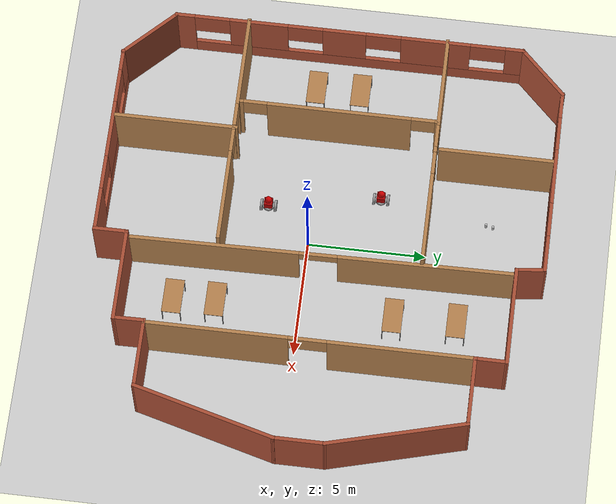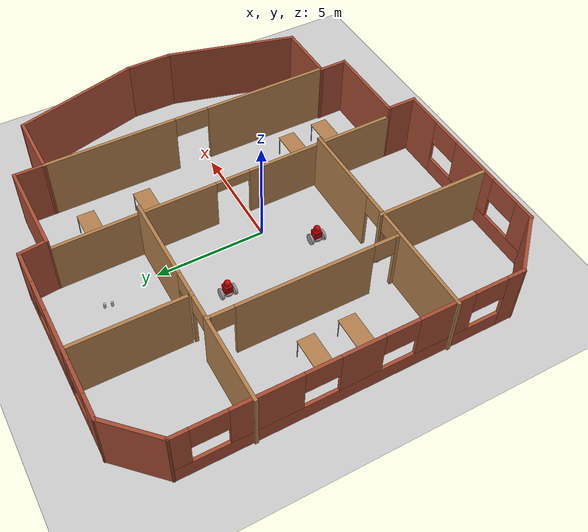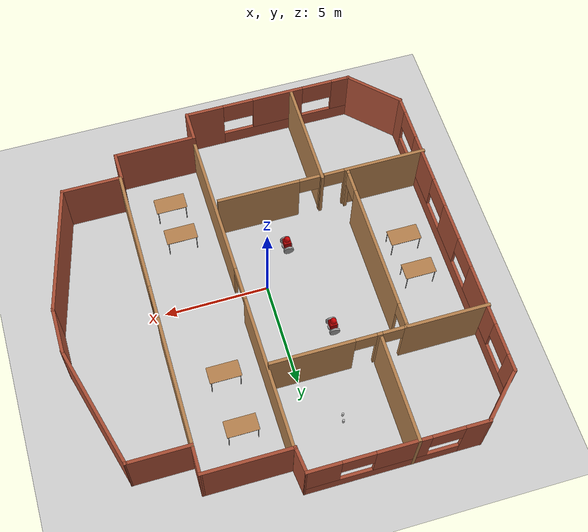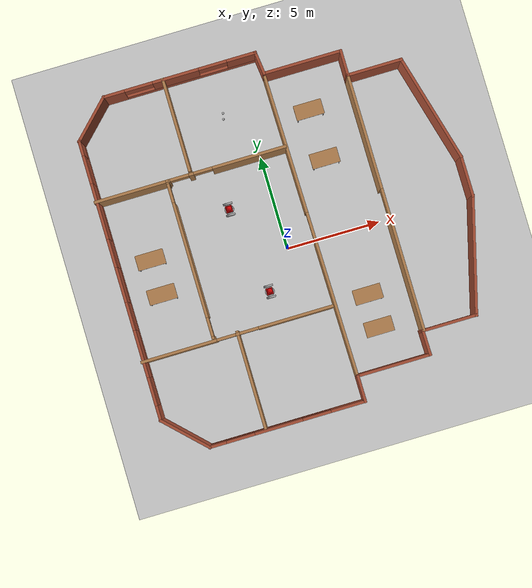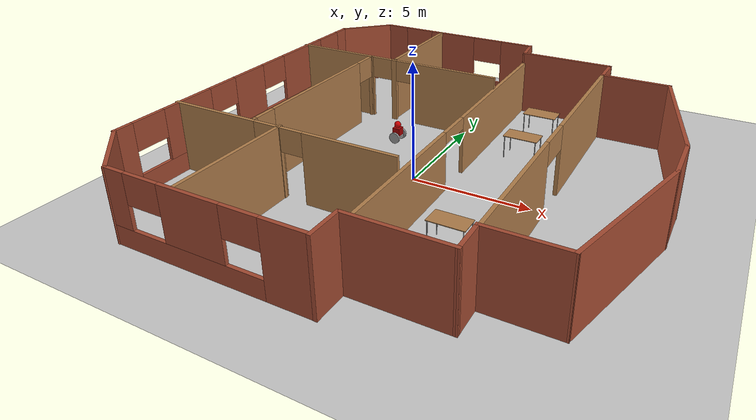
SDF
<sdf version="1.7">
 <world name="default">
  <plugin name="welcome_message" filename="libwelcome_message.so"/>
  <light name="sun" type="directional">
   <pose>0 0 10 0 -0 0</pose>
   <diffuse>0.8 0.8 0.8 1</diffuse>
   <specular>0.2 0.2 0.2 1</specular>
   <attenuation>
    <range>1000</range>
    <constant>0.9</constant>
    <linear>0.01</linear>
    <quadratic>0.001</quadratic>
   </attenuation>
   <direction>-0.5 0.1 -0.9</direction>
   <spot><inner_angle>0</inner_angle><outer_angle>0</outer_angle><falloff>0</falloff></spot>
  </light>
  <model name="ground_plane">
   <static>1</static>
   <link name="link">
    <collision name="collision">
     <geometry><plane><normal>0 0 1</normal><size>100 100</size></plane></geometry>
     <surface>
      <contact><collide_bitmask>65535</collide_bitmask></contact>
      <friction><ode><mu>100</mu><mu2>50</mu2></ode></friction>
     </surface>
    </collision>
    <visual name="visual">
     <cast_shadows>0</cast_shadows>
     <geometry><plane><normal>0 0 1</normal><size>100 100</size></plane></geometry>
     <material>
      <script><uri>file://media/materials/scripts/gazebo.material</uri><name>Gazebo/Grey</name></script>
     </material>
    </visual>
   </link>
  </model>
  <gravity>0 0 -9.8</gravity>
  <magnetic_field>6e-06 2.3e-05 -4.2e-05</magnetic_field>
  <atmosphere type="adiabatic"/>
  <physics type="ode">
   <max_step_size>0.001</max_step_size>
   <real_time_factor>1</real_time_factor>
   <real_time_update_rate>1000</real_time_update_rate>
  </physics>
  <scene><ambient>0.4 0.4 0.4 1</ambient><background>0.7 0.7 0.7 1</background><shadows>1</shadows></scene>
  <spherical_coordinates>
   <surface_model>EARTH_WGS84</surface_model>
   <latitude_deg>0</latitude_deg>
   <longitude_deg>0</longitude_deg>
   <elevation>0</elevation>
   <heading_deg>0</heading_deg>
  </spherical_coordinates>
  <model name="Building">
   <pose>0.522472 0.648664 0 0 -0 0</pose>
   <link name="Wall_0">
    <collision name="Wall_0_Collision">
     <geometry><box><size>4 0.15 3</size></box></geometry>
     <pose>0 0 1.5 0 -0 0</pose>
    </collision>
    <visual name="Wall_0_Visual">
     <pose>0 0 1.5 0 -0 0</pose>
     <geometry><box><size>4 0.15 3</size></box></geometry>
     <material>
      <script><uri>file://media/materials/scripts/gazebo.material</uri><name>Gazebo/Bricks</name></script>
      <ambient>1 1 1 1</ambient>
     </material>
     <meta><layer>0</layer></meta>
    </visual>
    <pose>2.95253 -8.01393 0 0 -0 3.14159</pose>
   </link>
   <link name="Wall_10">
    <collision name="Wall_10_Collision">
     <geometry><box><size>4.25 0.15 3</size></box></geometry>
     <pose>0 0 1.5 0 -0 0</pose>
    </collision>
    <visual name="Wall_10_Visual">
     <pose>0 0 1.5 0 -0 0</pose>
     <geometry><box><size>4.25 0.15 3</size></box></geometry>
     <material>
      <script><uri>file://media/materials/scripts/gazebo.material</uri><name>Gazebo/Bricks</name></script>
      <ambient>1 1 1 1</ambient>
     </material>
     <meta><layer>0</layer></meta>
    </visual>
    <pose>2.88353 8.19507 0 0 -0 0</pose>
   </link>
   <link name="Wall_13">
    <collision name="Wall_13_Collision">
     <geometry><box><size>3 0.15 3</size></box></geometry>
     <pose>0 0 1.5 0 -0 0</pose>
    </collision>
    <visual name="Wall_13_Visual">
     <pose>0 0 1.5 0 -0 0</pose>
     <geometry><box><size>3 0.15 3</size></box></geometry>
     <material>
      <script><uri>file://media/materials/scripts/gazebo.material</uri><name>Gazebo/Bricks</name></script>
      <ambient>1 1 1 1</ambient>
     </material>
     <meta><layer>0</layer></meta>
    </visual>
    <pose>6.35253 6.89207 0 0 -0 0</pose>
   </link>
   <link name="Wall_14">
    <collision name="Wall_14_Collision">
     <geometry><box><size>6 0.15 3</size></box></geometry>
     <pose>0 0 1.5 0 -0 0</pose>
    </collision>
    <visual name="Wall_14_Visual">
     <pose>0 0 1.5 0 -0 0</pose>
     <geometry><box><size>6 0.15 3</size></box></geometry>
     <material>
      <script><uri>file://media/materials/scripts/gazebo.material</uri><name>Gazebo/Bricks</name></script>
      <ambient>1 1 1 1</ambient>
     </material>
     <meta><layer>0</layer></meta>
    </visual>
    <pose>8.53453 4.06707 0 0 -0 -1.30898</pose>
   </link>
   <link name="Wall_15">
    <collision name="Wall_15_Collision">
     <geometry><box><size>2.25 0.15 3</size></box></geometry>
     <pose>0 0 1.5 0 -0 0</pose>
    </collision>
    <visual name="Wall_15_Visual">
     <pose>0 0 1.5 0 -0 0</pose>
     <geometry><box><size>2.25 0.15 3</size></box></geometry>
     <material>
      <script><uri>file://media/materials/scripts/gazebo.material</uri><name>Gazebo/Bricks</name></script>
      <ambient>1 1 1 1</ambient>
     </material>
     <meta><layer>0</layer></meta>
    </visual>
    <pose>9.29153 0.192069 0 0 -0 -1.5708</pose>
   </link>
   <link name="Wall_16">
    <collision name="Wall_16_Collision">
     <geometry><box><size>6.25 0.15 3</size></box></geometry>
     <pose>0 0 1.5 0 -0 0</pose>
    </collision>
    <visual name="Wall_16_Visual">
     <pose>0 0 1.5 0 -0 0</pose>
     <geometry><box><size>6.25 0.15 3</size></box></geometry>
     <material>
      <script><uri>file://media/materials/scripts/gazebo.material</uri><name>Gazebo/Bricks</name></script>
      <ambient>1 1 1 1</ambient>
     </material>
     <meta><layer>0</layer></meta>
    </visual>
    <pose>8.50203 -3.80393 0 0 -0 -1.83263</pose>
   </link>
   <link name="Wall_17">
    <collision name="Wall_17_Collision">
     <geometry><box><size>3 0.15 3</size></box></geometry>
     <pose>0 0 1.5 0 -0 0</pose>
    </collision>
    <visual name="Wall_17_Visual">
     <pose>0 0 1.5 0 -0 0</pose>
     <geometry><box><size>3 0.15 3</size></box></geometry>
     <material>
      <script><uri>file://media/materials/scripts/gazebo.material</uri><name>Gazebo/Bricks</name></script>
      <ambient>1 1 1 1</ambient>
     </material>
     <meta><layer>0</layer></meta>
    </visual>
    <pose>6.28753 -6.74993 0 0 -0 3.14159</pose>
   </link>
   <link name="Wall_21">
    <pose>-4.25847 4.28707 0 0 -0 0</pose>
    <visual name="Wall_21_Visual_0">
     <pose>-3.10441 0 1.5 0 -0 0</pose>
     <geometry><box><size>4.04118 0.15 3</size></box></geometry>
     <material>
      <script><uri>file://media/materials/scripts/gazebo.material</uri><name>Gazebo/Wood</name></script>
      <ambient>0.360784 0.207843 0.4 1</ambient>
     </material>
     <meta><layer>0</layer></meta>
    </visual>
    <collision name="Wall_21_Collision_0">
     <geometry><box><size>4.04118 0.15 3</size></box></geometry>
     <pose>-3.10441 0 1.5 0 -0 0</pose>
    </collision>
    <visual name="Wall_21_Visual_1">
     <pose>0.044252 0 1.5 0 -0 0</pose>
     <geometry><box><size>0.256146 0.15 3</size></box></geometry>
     <material>
      <script><uri>file://media/materials/scripts/gazebo.material</uri><name>Gazebo/Wood</name></script>
      <ambient>0.360784 0.207843 0.4 1</ambient>
     </material>
     <meta><layer>0</layer></meta>
    </visual>
    <collision name="Wall_21_Collision_1">
     <geometry><box><size>0.256146 0.15 3</size></box></geometry>
     <pose>0.044252 0 1.5 0 -0 0</pose>
    </collision>
    <visual name="Wall_21_Visual_2">
     <pose>3.14866 0 1.5 0 -0 0</pose>
     <geometry><box><size>3.95268 0.15 3</size></box></geometry>
     <material>
      <script><uri>file://media/materials/scripts/gazebo.material</uri><name>Gazebo/Wood</name></script>
      <ambient>0.360784 0.207843 0.4 1</ambient>
     </material>
     <meta><layer>0</layer></meta>
    </visual>
    <collision name="Wall_21_Collision_2">
     <geometry><box><size>3.95268 0.15 3</size></box></geometry>
     <pose>3.14866 0 1.5 0 -0 0</pose>
    </collision>
    <visual name="Wall_21_Visual_3">
     <pose>-0.583821 0 2.5 0 -0 0</pose>
     <geometry><box><size>1 0.15 1</size></box></geometry>
     <material>
      <script><uri>file://media/materials/scripts/gazebo.material</uri><name>Gazebo/Wood</name></script>
      <ambient>0.360784 0.207843 0.4 1</ambient>
     </material>
     <meta><layer>0</layer></meta>
    </visual>
    <collision name="Wall_21_Collision_3">
     <geometry><box><size>1 0.15 1</size></box></geometry>
     <pose>-0.583821 0 2.5 0 -0 0</pose>
    </collision>
    <visual name="Wall_21_Visual_4">
     <pose>0.672325 0 2.5 0 -0 0</pose>
     <geometry><box><size>1 0.15 1</size></box></geometry>
     <material>
      <script><uri>file://media/materials/scripts/gazebo.material</uri><name>Gazebo/Wood</name></script>
      <ambient>0.360784 0.207843 0.4 1</ambient>
     </material>
     <meta><layer>0</layer></meta>
    </visual>
    <collision name="Wall_21_Collision_4">
     <geometry><box><size>1 0.15 1</size></box></geometry>
     <pose>0.672325 0 2.5 0 -0 0</pose>
    </collision>
   </link>
   <link name="Wall_23">
    <pose>-4.25847 -4.22693 0 0 -0 0</pose>
    <visual name="Wall_23_Visual_0">
     <pose>-3.10441 0 1.5 0 -0 0</pose>
     <geometry><box><size>4.04118 0.15 3</size></box></geometry>
     <material>
      <script><uri>file://media/materials/scripts/gazebo.material</uri><name>Gazebo/Wood</name></script>
      <ambient>0.360784 0.207843 0.4 1</ambient>
     </material>
     <meta><layer>0</layer></meta>
    </visual>
    <collision name="Wall_23_Collision_0">
     <geometry><box><size>4.04118 0.15 3</size></box></geometry>
     <pose>-3.10441 0 1.5 0 -0 0</pose>
    </collision>
    <visual name="Wall_23_Visual_1">
     <pose>0.02099 0 1.5 0 -0 0</pose>
     <geometry><box><size>0.209622 0.15 3</size></box></geometry>
     <material>
      <script><uri>file://media/materials/scripts/gazebo.material</uri><name>Gazebo/Wood</name></script>
      <ambient>0.360784 0.207843 0.4 1</ambient>
     </material>
     <meta><layer>0</layer></meta>
    </visual>
    <collision name="Wall_23_Collision_1">
     <geometry><box><size>0.209622 0.15 3</size></box></geometry>
     <pose>0.02099 0 1.5 0 -0 0</pose>
    </collision>
    <visual name="Wall_23_Visual_2">
     <pose>3.1254 0 1.5 0 -0 0</pose>
     <geometry><box><size>3.9992 0.15 3</size></box></geometry>
     <material>
      <script><uri>file://media/materials/scripts/gazebo.material</uri><name>Gazebo/Wood</name></script>
      <ambient>0.360784 0.207843 0.4 1</ambient>
     </material>
     <meta><layer>0</layer></meta>
    </visual>
    <collision name="Wall_23_Collision_2">
     <geometry><box><size>3.9992 0.15 3</size></box></geometry>
     <pose>3.1254 0 1.5 0 -0 0</pose>
    </collision>
    <visual name="Wall_23_Visual_3">
     <pose>-0.583821 0 2.5 0 -0 0</pose>
     <geometry><box><size>1 0.15 1</size></box></geometry>
     <material>
      <script><uri>file://media/materials/scripts/gazebo.material</uri><name>Gazebo/Wood</name></script>
      <ambient>0.360784 0.207843 0.4 1</ambient>
     </material>
     <meta><layer>0</layer></meta>
    </visual>
    <collision name="Wall_23_Collision_3">
     <geometry><box><size>1 0.15 1</size></box></geometry>
     <pose>-0.583821 0 2.5 0 -0 0</pose>
    </collision>
    <visual name="Wall_23_Visual_4">
     <pose>0.625801 0 2.5 0 -0 0</pose>
     <geometry><box><size>1 0.15 1</size></box></geometry>
     <material>
      <script><uri>file://media/materials/scripts/gazebo.material</uri><name>Gazebo/Wood</name></script>
      <ambient>0.360784 0.207843 0.4 1</ambient>
     </material>
     <meta><layer>0</layer></meta>
    </visual>
    <collision name="Wall_23_Collision_4">
     <geometry><box><size>1 0.15 1</size></box></geometry>
     <pose>0.625801 0 2.5 0 -0 0</pose>
    </collision>
   </link>
   <link name="Wall_27">
    <collision name="Wall_27_Collision">
     <geometry><box><size>5 0.15 3</size></box></geometry>
     <pose>0 0 1.5 0 -0 0</pose>
    </collision>
    <visual name="Wall_27_Visual">
     <pose>0 0 1.5 0 -0 0</pose>
     <geometry><box><size>5 0.15 3</size></box></geometry>
     <material>
      <script><uri>file://media/materials/scripts/gazebo.material</uri><name>Gazebo/Wood</name></script>
      <ambient>0.360784 0.207843 0.4 1</ambient>
     </material>
     <meta><layer>0</layer></meta>
    </visual>
    <pose>-4.23747 6.93307 0 0 -0 -1.5708</pose>
   </link>
   <link name="Wall_29">
    <pose>-5.49347 0.112069 0 0 -0 -1.5708</pose>
    <visual name="Wall_29_Visual_0">
     <pose>-4.13689 0 1.5 0 -0 0</pose>
     <geometry><box><size>0.22622 0.15 3</size></box></geometry>
     <material>
      <script><uri>file://media/materials/scripts/gazebo.material</uri><name>Gazebo/Wood</name></script>
      <ambient>0.360784 0.207843 0.4 1</ambient>
     </material>
     <meta><layer>0</layer></meta>
    </visual>
    <collision name="Wall_29_Collision_0">
     <geometry><box><size>0.22622 0.15 3</size></box></geometry>
     <pose>-4.13689 0 1.5 0 -0 0</pose>
    </collision>
    <visual name="Wall_29_Visual_1">
     <pose>0.0353 0 1.5 0 -0 0</pose>
     <geometry><box><size>6.11816 0.15 3</size></box></geometry>
     <material>
      <script><uri>file://media/materials/scripts/gazebo.material</uri><name>Gazebo/Wood</name></script>
      <ambient>0.360784 0.207843 0.4 1</ambient>
     </material>
     <meta><layer>0</layer></meta>
    </visual>
    <collision name="Wall_29_Collision_1">
     <geometry><box><size>6.11816 0.15 3</size></box></geometry>
     <pose>0.0353 0 1.5 0 -0 0</pose>
    </collision>
    <visual name="Wall_29_Visual_2">
     <pose>4.17219 0 1.5 0 -0 0</pose>
     <geometry><box><size>0.155621 0.15 3</size></box></geometry>
     <material>
      <script><uri>file://media/materials/scripts/gazebo.material</uri><name>Gazebo/Wood</name></script>
      <ambient>0.360784 0.207843 0.4 1</ambient>
     </material>
     <meta><layer>0</layer></meta>
    </visual>
    <collision name="Wall_29_Collision_2">
     <geometry><box><size>0.155621 0.15 3</size></box></geometry>
     <pose>4.17219 0 1.5 0 -0 0</pose>
    </collision>
    <visual name="Wall_29_Visual_3">
     <pose>-3.52378 0 2.5 0 -0 0</pose>
     <geometry><box><size>1 0.15 1</size></box></geometry>
     <material>
      <script><uri>file://media/materials/scripts/gazebo.material</uri><name>Gazebo/Wood</name></script>
      <ambient>0.360784 0.207843 0.4 1</ambient>
     </material>
     <meta><layer>0</layer></meta>
    </visual>
    <collision name="Wall_29_Collision_3">
     <geometry><box><size>1 0.15 1</size></box></geometry>
     <pose>-3.52378 0 2.5 0 -0 0</pose>
    </collision>
    <visual name="Wall_29_Visual_4">
     <pose>3.59438 0 2.5 0 -0 0</pose>
     <geometry><box><size>1 0.15 1</size></box></geometry>
     <material>
      <script><uri>file://media/materials/scripts/gazebo.material</uri><name>Gazebo/Wood</name></script>
      <ambient>0.360784 0.207843 0.4 1</ambient>
     </material>
     <meta><layer>0</layer></meta>
    </visual>
    <collision name="Wall_29_Collision_4">
     <geometry><box><size>1 0.15 1</size></box></geometry>
     <pose>3.59438 0 2.5 0 -0 0</pose>
    </collision>
   </link>
   <link name="Wall_3">
    <pose>-3.16947 -9.35193 0 0 -0 3.14159</pose>
    <visual name="Wall_3_Visual_0">
     <pose>-3.25269 0 1.5 0 -0 0</pose>
     <geometry><box><size>1.74462 0.15 3</size></box></geometry>
     <material>
      <script><uri>file://media/materials/scripts/gazebo.material</uri><name>Gazebo/Bricks</name></script>
      <ambient>1 1 1 1</ambient>
     </material>
     <meta><layer>0</layer></meta>
    </visual>
    <collision name="Wall_3_Collision_0">
     <geometry><box><size>1.74462 0.15 3</size></box></geometry>
     <pose>-3.25269 0 1.5 0 -0 0</pose>
    </collision>
    <visual name="Wall_3_Visual_1">
     <pose>0.872312 0 0.4 0 -0 0</pose>
     <geometry><box><size>6.50538 0.15 0.8</size></box></geometry>
     <material>
      <script><uri>file://media/materials/scripts/gazebo.material</uri><name>Gazebo/Bricks</name></script>
      <ambient>1 1 1 1</ambient>
     </material>
     <meta><layer>0</layer></meta>
    </visual>
    <collision name="Wall_3_Collision_1">
     <geometry><box><size>6.50538 0.15 0.8</size></box></geometry>
     <pose>0.872312 0 0.4 0 -0 0</pose>
    </collision>
    <visual name="Wall_3_Visual_2">
     <pose>0.393413 0 1.9 0 -0 0</pose>
     <geometry><box><size>2.54758 0.15 2.2</size></box></geometry>
     <material>
      <script><uri>file://media/materials/scripts/gazebo.material</uri><name>Gazebo/Bricks</name></script>
      <ambient>1 1 1 1</ambient>
     </material>
     <meta><layer>0</layer></meta>
    </visual>
    <collision name="Wall_3_Collision_2">
     <geometry><box><size>2.54758 0.15 2.2</size></box></geometry>
     <pose>0.393413 0 1.9 0 -0 0</pose>
    </collision>
    <visual name="Wall_3_Visual_3">
     <pose>3.6461 0 1.9 0 -0 0</pose>
     <geometry><box><size>0.957797 0.15 2.2</size></box></geometry>
     <material>
      <script><uri>file://media/materials/scripts/gazebo.material</uri><name>Gazebo/Bricks</name></script>
      <ambient>1 1 1 1</ambient>
     </material>
     <meta><layer>0</layer></meta>
    </visual>
    <collision name="Wall_3_Collision_3">
     <geometry><box><size>0.957797 0.15 2.2</size></box></geometry>
     <pose>3.6461 0 1.9 0 -0 0</pose>
    </collision>
    <visual name="Wall_3_Visual_4">
     <pose>-1.63038 0 2.4 0 -0 0</pose>
     <geometry><box><size>1.5 0.15 1.2</size></box></geometry>
     <material>
      <script><uri>file://media/materials/scripts/gazebo.material</uri><name>Gazebo/Bricks</name></script>
      <ambient>1 1 1 1</ambient>
     </material>
     <meta><layer>0</layer></meta>
    </visual>
    <collision name="Wall_3_Collision_4">
     <geometry><box><size>1.5 0.15 1.2</size></box></geometry>
     <pose>-1.63038 0 2.4 0 -0 0</pose>
    </collision>
    <visual name="Wall_3_Visual_5">
     <pose>2.4172 0 2.4 0 -0 0</pose>
     <geometry><box><size>1.5 0.15 1.2</size></box></geometry>
     <material>
      <script><uri>file://media/materials/scripts/gazebo.material</uri><name>Gazebo/Bricks</name></script>
      <ambient>1 1 1 1</ambient>
     </material>
     <meta><layer>0</layer></meta>
    </visual>
    <collision name="Wall_3_Collision_5">
     <geometry><box><size>1.5 0.15 1.2</size></box></geometry>
     <pose>2.4172 0 2.4 0 -0 0</pose>
    </collision>
   </link>
   <link name="Wall_31">
    <collision name="Wall_31_Collision">
     <geometry><box><size>5.25 0.15 3</size></box></geometry>
     <pose>0 0 1.5 0 -0 0</pose>
    </collision>
    <visual name="Wall_31_Visual">
     <pose>0 0 1.5 0 -0 0</pose>
     <geometry><box><size>5.25 0.15 3</size></box></geometry>
     <material>
      <script><uri>file://media/materials/scripts/gazebo.material</uri><name>Gazebo/Wood</name></script>
      <ambient>0.360784 0.207843 0.4 1</ambient>
     </material>
     <meta><layer>0</layer></meta>
    </visual>
    <pose>-4.23747 -6.68393 0 0 -0 -1.5708</pose>
   </link>
   <link name="Wall_35">
    <collision name="Wall_35_Collision">
     <geometry><box><size>1.5 0.15 3</size></box></geometry>
     <pose>0 0 1.5 0 -0 0</pose>
    </collision>
    <visual name="Wall_35_Visual">
     <pose>0 0 1.5 0 -0 0</pose>
     <geometry><box><size>1.5 0.15 3</size></box></geometry>
     <material>
      <script><uri>file://media/materials/scripts/gazebo.material</uri><name>Gazebo/Bricks</name></script>
      <ambient>1 1 1 1</ambient>
     </material>
     <meta><layer>0</layer></meta>
    </visual>
    <pose>1.02753 -8.68893 0 0 -0 -1.5708</pose>
   </link>
   <link name="Wall_40">
    <collision name="Wall_40_Collision">
     <geometry><box><size>1.31428 0.15 3</size></box></geometry>
     <pose>0 0 1.5 0 -0 0</pose>
    </collision>
    <visual name="Wall_40_Visual">
     <pose>0 0 1.5 0 -0 0</pose>
     <geometry><box><size>1.31428 0.15 3</size></box></geometry>
     <material>
      <script><uri>file://media/materials/scripts/gazebo.material</uri><name>Gazebo/Bricks</name></script>
      <ambient>1 1 1 1</ambient>
     </material>
     <meta><layer>0</layer></meta>
    </visual>
    <pose>0.768529 8.77357 0 0 -0 -1.45891</pose>
   </link>
   <link name="Wall_42">
    <pose>0.930529 0.090569 0 0 -0 -1.55883</pose>
    <visual name="Wall_42_Visual_0">
     <pose>-4.42557 0 1.25 0 -0 0</pose>
     <geometry><box><size>7.50902 0.15 2.5</size></box></geometry>
     <material>
      <script><uri>file://media/materials/scripts/gazebo.material</uri><name>Gazebo/Wood</name></script>
      <ambient>0.360784 0.207843 0.4 1</ambient>
     </material>
     <meta><layer>0</layer></meta>
    </visual>
    <collision name="Wall_42_Collision_0">
     <geometry><box><size>7.50902 0.15 2.5</size></box></geometry>
     <pose>-4.42557 0 1.25 0 -0 0</pose>
    </collision>
    <visual name="Wall_42_Visual_1">
     <pose>4.55451 0 1.25 0 -0 0</pose>
     <geometry><box><size>7.25114 0.15 2.5</size></box></geometry>
     <material>
      <script><uri>file://media/materials/scripts/gazebo.material</uri><name>Gazebo/Wood</name></script>
      <ambient>0.360784 0.207843 0.4 1</ambient>
     </material>
     <meta><layer>0</layer></meta>
    </visual>
    <collision name="Wall_42_Collision_1">
     <geometry><box><size>7.25114 0.15 2.5</size></box></geometry>
     <pose>4.55451 0 1.25 0 -0 0</pose>
    </collision>
    <visual name="Wall_42_Visual_2">
     <pose>0.12894 0 2.25 0 -0 0</pose>
     <geometry><box><size>1.6 0.15 0.5</size></box></geometry>
     <material>
      <script><uri>file://media/materials/scripts/gazebo.material</uri><name>Gazebo/Wood</name></script>
      <ambient>0.360784 0.207843 0.4 1</ambient>
     </material>
     <meta><layer>0</layer></meta>
    </visual>
    <collision name="Wall_42_Collision_2">
     <geometry><box><size>1.6 0.15 0.5</size></box></geometry>
     <pose>0.12894 0 2.25 0 -0 0</pose>
    </collision>
   </link>
   <link name="Wall_44">
    <collision name="Wall_44_Collision">
     <geometry><box><size>1.41409 0.15 3</size></box></geometry>
     <pose>0 0 1.5 0 -0 0</pose>
    </collision>
    <visual name="Wall_44_Visual">
     <pose>0 0 1.5 0 -0 0</pose>
     <geometry><box><size>1.41409 0.15 3</size></box></geometry>
     <material>
      <script><uri>file://media/materials/scripts/gazebo.material</uri><name>Gazebo/Bricks</name></script>
      <ambient>1 1 1 1</ambient>
     </material>
     <meta><layer>0</layer></meta>
    </visual>
    <pose>4.87003 -7.38193 0 0 -0 -1.55893</pose>
   </link>
   <link name="Wall_46">
    <collision name="Wall_46_Collision">
     <geometry><box><size>1.45301 0.15 3</size></box></geometry>
     <pose>0 0 1.5 0 -0 0</pose>
    </collision>
    <visual name="Wall_46_Visual">
     <pose>0 0 1.5 0 -0 0</pose>
     <geometry><box><size>1.45301 0.15 3</size></box></geometry>
     <material>
      <script><uri>file://media/materials/scripts/gazebo.material</uri><name>Gazebo/Bricks</name></script>
      <ambient>1 1 1 1</ambient>
     </material>
     <meta><layer>0</layer></meta>
    </visual>
    <pose>4.93053 7.54357 0 0 -0 -1.5754</pose>
   </link>
   <link name="Wall_48">
    <pose>4.92753 0.092069 0 0 -0 -1.5708</pose>
    <visual name="Wall_48_Visual_0">
     <pose>-3.79496 0 1.5 0 -0 0</pose>
     <geometry><box><size>6.16008 0.15 3</size></box></geometry>
     <material>
      <script><uri>file://media/materials/scripts/gazebo.material</uri><name>Gazebo/Wood</name></script>
      <ambient>0.360784 0.207843 0.4 1</ambient>
     </material>
     <meta><layer>0</layer></meta>
    </visual>
    <collision name="Wall_48_Collision_0">
     <geometry><box><size>6.16008 0.15 3</size></box></geometry>
     <pose>-3.79496 0 1.5 0 -0 0</pose>
    </collision>
    <visual name="Wall_48_Visual_1">
     <pose>3.88004 0 1.5 0 -0 0</pose>
     <geometry><box><size>5.98991 0.15 3</size></box></geometry>
     <material>
      <script><uri>file://media/materials/scripts/gazebo.material</uri><name>Gazebo/Wood</name></script>
      <ambient>0.360784 0.207843 0.4 1</ambient>
     </material>
     <meta><layer>0</layer></meta>
    </visual>
    <collision name="Wall_48_Collision_1">
     <geometry><box><size>5.98991 0.15 3</size></box></geometry>
     <pose>3.88004 0 1.5 0 -0 0</pose>
    </collision>
    <visual name="Wall_48_Visual_2">
     <pose>0.085085 0 2.5 0 -0 0</pose>
     <geometry><box><size>1.6 0.15 1</size></box></geometry>
     <material>
      <script><uri>file://media/materials/scripts/gazebo.material</uri><name>Gazebo/Wood</name></script>
      <ambient>0.360784 0.207843 0.4 1</ambient>
     </material>
     <meta><layer>0</layer></meta>
    </visual>
    <collision name="Wall_48_Collision_2">
     <geometry><box><size>1.6 0.15 1</size></box></geometry>
     <pose>0.085085 0 2.5 0 -0 0</pose>
    </collision>
   </link>
   <link name="Wall_5">
    <collision name="Wall_5_Collision">
     <geometry><box><size>3 0.15 3</size></box></geometry>
     <pose>0 0 1.5 0 -0 0</pose>
    </collision>
    <visual name="Wall_5_Visual">
     <pose>0 0 1.5 0 -0 0</pose>
     <geometry><box><size>3 0.15 3</size></box></geometry>
     <material>
      <script><uri>file://media/materials/scripts/gazebo.material</uri><name>Gazebo/Bricks</name></script>
      <ambient>1 1 1 1</ambient>
     </material>
     <meta><layer>0</layer></meta>
    </visual>
    <pose>-8.22747 -8.34443 0 0 -0 2.35644</pose>
   </link>
   <link name="Wall_6">
    <pose>-9.23547 0.088069 0 0 -0 1.5708</pose>
    <visual name="Wall_6_Visual_0">
     <pose>-7.07329 0 1.5 0 -0 0</pose>
     <geometry><box><size>0.853425 0.15 3</size></box></geometry>
     <material>
      <script><uri>file://media/materials/scripts/gazebo.material</uri><name>Gazebo/Bricks</name></script>
      <ambient>1 1 1 1</ambient>
     </material>
     <meta><layer>0</layer></meta>
    </visual>
    <collision name="Wall_6_Collision_0">
     <geometry><box><size>0.853425 0.15 3</size></box></geometry>
     <pose>-7.07329 0 1.5 0 -0 0</pose>
    </collision>
    <visual name="Wall_6_Visual_1">
     <pose>0.426713 0 0.4 0 -0 0</pose>
     <geometry><box><size>14.1466 0.15 0.8</size></box></geometry>
     <material>
      <script><uri>file://media/materials/scripts/gazebo.material</uri><name>Gazebo/Bricks</name></script>
      <ambient>1 1 1 1</ambient>
     </material>
     <meta><layer>0</layer></meta>
    </visual>
    <collision name="Wall_6_Collision_1">
     <geometry><box><size>14.1466 0.15 0.8</size></box></geometry>
     <pose>0.426713 0 0.4 0 -0 0</pose>
    </collision>
    <visual name="Wall_6_Visual_2">
     <pose>-3.89605 0 1.9 0 -0 0</pose>
     <geometry><box><size>2.50106 0.15 2.2</size></box></geometry>
     <material>
      <script><uri>file://media/materials/scripts/gazebo.material</uri><name>Gazebo/Bricks</name></script>
      <ambient>1 1 1 1</ambient>
     </material>
     <meta><layer>0</layer></meta>
    </visual>
    <collision name="Wall_6_Collision_2">
     <geometry><box><size>2.50106 0.15 2.2</size></box></geometry>
     <pose>-3.89605 0 1.9 0 -0 0</pose>
    </collision>
    <visual name="Wall_6_Visual_3">
     <pose>-0.220657 0 1.9 0 -0 0</pose>
     <geometry><box><size>1.84972 0.15 2.2</size></box></geometry>
     <material>
      <script><uri>file://media/materials/scripts/gazebo.material</uri><name>Gazebo/Bricks</name></script>
      <ambient>1 1 1 1</ambient>
     </material>
     <meta><layer>0</layer></meta>
    </visual>
    <collision name="Wall_6_Collision_3">
     <geometry><box><size>1.84972 0.15 2.2</size></box></geometry>
     <pose>-0.220657 0 1.9 0 -0 0</pose>
    </collision>
    <visual name="Wall_6_Visual_4">
     <pose>3.68735 0 1.9 0 -0 0</pose>
     <geometry><box><size>2.9663 0.15 2.2</size></box></geometry>
     <material>
      <script><uri>file://media/materials/scripts/gazebo.material</uri><name>Gazebo/Bricks</name></script>
      <ambient>1 1 1 1</ambient>
     </material>
     <meta><layer>0</layer></meta>
    </visual>
    <collision name="Wall_6_Collision_4">
     <geometry><box><size>2.9663 0.15 2.2</size></box></geometry>
     <pose>3.68735 0 1.9 0 -0 0</pose>
    </collision>
    <visual name="Wall_6_Visual_5">
     <pose>7.08525 0 1.9 0 -0 0</pose>
     <geometry><box><size>0.8295 0.15 2.2</size></box></geometry>
     <material>
      <script><uri>file://media/materials/scripts/gazebo.material</uri><name>Gazebo/Bricks</name></script>
      <ambient>1 1 1 1</ambient>
     </material>
     <meta><layer>0</layer></meta>
    </visual>
    <collision name="Wall_6_Collision_5">
     <geometry><box><size>0.8295 0.15 2.2</size></box></geometry>
     <pose>7.08525 0 1.9 0 -0 0</pose>
    </collision>
    <visual name="Wall_6_Visual_6">
     <pose>-5.89658 0 2.4 0 -0 0</pose>
     <geometry><box><size>1.5 0.15 1.2</size></box></geometry>
     <material>
      <script><uri>file://media/materials/scripts/gazebo.material</uri><name>Gazebo/Bricks</name></script>
      <ambient>1 1 1 1</ambient>
     </material>
     <meta><layer>0</layer></meta>
    </visual>
    <collision name="Wall_6_Collision_6">
     <geometry><box><size>1.5 0.15 1.2</size></box></geometry>
     <pose>-5.89658 0 2.4 0 -0 0</pose>
    </collision>
    <visual name="Wall_6_Visual_7">
     <pose>-1.89552 0 2.4 0 -0 0</pose>
     <geometry><box><size>1.5 0.15 1.2</size></box></geometry>
     <material>
      <script><uri>file://media/materials/scripts/gazebo.material</uri><name>Gazebo/Bricks</name></script>
      <ambient>1 1 1 1</ambient>
     </material>
     <meta><layer>0</layer></meta>
    </visual>
    <collision name="Wall_6_Collision_7">
     <geometry><box><size>1.5 0.15 1.2</size></box></geometry>
     <pose>-1.89552 0 2.4 0 -0 0</pose>
    </collision>
    <visual name="Wall_6_Visual_8">
     <pose>1.4542 0 2.4 0 -0 0</pose>
     <geometry><box><size>1.5 0.15 1.2</size></box></geometry>
     <material>
      <script><uri>file://media/materials/scripts/gazebo.material</uri><name>Gazebo/Bricks</name></script>
      <ambient>1 1 1 1</ambient>
     </material>
     <meta><layer>0</layer></meta>
    </visual>
    <collision name="Wall_6_Collision_8">
     <geometry><box><size>1.5 0.15 1.2</size></box></geometry>
     <pose>1.4542 0 2.4 0 -0 0</pose>
    </collision>
    <visual name="Wall_6_Visual_9">
     <pose>5.9205 0 2.4 0 -0 0</pose>
     <geometry><box><size>1.5 0.15 1.2</size></box></geometry>
     <material>
      <script><uri>file://media/materials/scripts/gazebo.material</uri><name>Gazebo/Bricks</name></script>
      <ambient>1 1 1 1</ambient>
     </material>
     <meta><layer>0</layer></meta>
    </visual>
    <collision name="Wall_6_Collision_9">
     <geometry><box><size>1.5 0.15 1.2</size></box></geometry>
     <pose>5.9205 0 2.4 0 -0 0</pose>
    </collision>
   </link>
   <link name="Wall_7">
    <collision name="Wall_7_Collision">
     <geometry><box><size>2.75 0.15 3</size></box></geometry>
     <pose>0 0 1.5 0 -0 0</pose>
    </collision>
    <visual name="Wall_7_Visual">
     <pose>0 0 1.5 0 -0 0</pose>
     <geometry><box><size>2.75 0.15 3</size></box></geometry>
     <material>
      <script><uri>file://media/materials/scripts/gazebo.material</uri><name>Gazebo/Bricks</name></script>
      <ambient>1 1 1 1</ambient>
     </material>
     <meta><layer>0</layer></meta>
    </visual>
    <pose>-8.31597 8.43257 0 0 -0 0.785398</pose>
   </link>
   <link name="Wall_8">
    <pose>-3.34647 9.35207 0 0 -0 0</pose>
    <visual name="Wall_8_Visual_0">
     <pose>-3.53434 0 1.5 0 -0 0</pose>
     <geometry><box><size>1.18132 0.15 3</size></box></geometry>
     <material>
      <script><uri>file://media/materials/scripts/gazebo.material</uri><name>Gazebo/Bricks</name></script>
      <ambient>1 1 1 1</ambient>
     </material>
     <meta><layer>0</layer></meta>
    </visual>
    <collision name="Wall_8_Collision_0">
     <geometry><box><size>1.18132 0.15 3</size></box></geometry>
     <pose>-3.53434 0 1.5 0 -0 0</pose>
    </collision>
    <visual name="Wall_8_Visual_1">
     <pose>0.59066 0 0.4 0 -0 0</pose>
     <geometry><box><size>7.06868 0.15 0.8</size></box></geometry>
     <material>
      <script><uri>file://media/materials/scripts/gazebo.material</uri><name>Gazebo/Bricks</name></script>
      <ambient>1 1 1 1</ambient>
     </material>
     <meta><layer>0</layer></meta>
    </visual>
    <collision name="Wall_8_Collision_1">
     <geometry><box><size>7.06868 0.15 0.8</size></box></geometry>
     <pose>0.59066 0 0.4 0 -0 0</pose>
    </collision>
    <visual name="Wall_8_Visual_2">
     <pose>-0.216413 0 1.9 0 -0 0</pose>
     <geometry><box><size>2.45453 0.15 2.2</size></box></geometry>
     <material>
      <script><uri>file://media/materials/scripts/gazebo.material</uri><name>Gazebo/Bricks</name></script>
      <ambient>1 1 1 1</ambient>
     </material>
     <meta><layer>0</layer></meta>
    </visual>
    <collision name="Wall_8_Collision_2">
     <geometry><box><size>2.45453 0.15 2.2</size></box></geometry>
     <pose>-0.216413 0 1.9 0 -0 0</pose>
    </collision>
    <visual name="Wall_8_Visual_3">
     <pose>3.31793 0 1.9 0 -0 0</pose>
     <geometry><box><size>1.61415 0.15 2.2</size></box></geometry>
     <material>
      <script><uri>file://media/materials/scripts/gazebo.material</uri><name>Gazebo/Bricks</name></script>
      <ambient>1 1 1 1</ambient>
     </material>
     <meta><layer>0</layer></meta>
    </visual>
    <collision name="Wall_8_Collision_3">
     <geometry><box><size>1.61415 0.15 2.2</size></box></geometry>
     <pose>3.31793 0 1.9 0 -0 0</pose>
    </collision>
    <visual name="Wall_8_Visual_4">
     <pose>-2.19368 0 2.4 0 -0 0</pose>
     <geometry><box><size>1.5 0.15 1.2</size></box></geometry>
     <material>
      <script><uri>file://media/materials/scripts/gazebo.material</uri><name>Gazebo/Bricks</name></script>
      <ambient>1 1 1 1</ambient>
     </material>
     <meta><layer>0</layer></meta>
    </visual>
    <collision name="Wall_8_Collision_4">
     <geometry><box><size>1.5 0.15 1.2</size></box></geometry>
     <pose>-2.19368 0 2.4 0 -0 0</pose>
    </collision>
    <visual name="Wall_8_Visual_5">
     <pose>1.76085 0 2.4 0 -0 0</pose>
     <geometry><box><size>1.5 0.15 1.2</size></box></geometry>
     <material>
      <script><uri>file://media/materials/scripts/gazebo.material</uri><name>Gazebo/Bricks</name></script>
      <ambient>1 1 1 1</ambient>
     </material>
     <meta><layer>0</layer></meta>
    </visual>
    <collision name="Wall_8_Collision_5">
     <geometry><box><size>1.5 0.15 1.2</size></box></geometry>
     <pose>1.76085 0 2.4 0 -0 0</pose>
    </collision>
   </link>
   <static>1</static>
  </model>
  <model name="table">
   <static>1</static>
   <link name="link">
    <collision name="surface">
     <pose>0 0 1 0 -0 0</pose>
     <geometry><box><size>1.5 0.8 0.03</size></box></geometry>
     <surface><friction><ode><mu>0.6</mu><mu2>0.6</mu2></ode></friction></surface>
    </collision>
    <visual name="visual1">
     <pose>0 0 1 0 -0 0</pose>
     <geometry><box><size>1.5 0.8 0.03</size></box></geometry>
     <material>
      <script><uri>file://media/materials/scripts/gazebo.material</uri><name>Gazebo/Wood</name></script>
     </material>
    </visual>
    <collision name="front_left_leg">
     <pose>0.68 0.38 0.5 0 -0 0</pose>
     <geometry><cylinder><radius>0.02</radius><length>1</length></cylinder></geometry>
    </collision>
    <visual name="front_left_leg">
     <pose>0.68 0.38 0.5 0 -0 0</pose>
     <geometry><cylinder><radius>0.02</radius><length>1</length></cylinder></geometry>
     <material>
      <script><uri>file://media/materials/scripts/gazebo.material</uri><name>Gazebo/Grey</name></script>
     </material>
    </visual>
    <collision name="front_right_leg">
     <pose>0.68 -0.38 0.5 0 -0 0</pose>
     <geometry><cylinder><radius>0.02</radius><length>1</length></cylinder></geometry>
    </collision>
    <visual name="front_right_leg">
     <pose>0.68 -0.38 0.5 0 -0 0</pose>
     <geometry><cylinder><radius>0.02</radius><length>1</length></cylinder></geometry>
     <material>
      <script><uri>file://media/materials/scripts/gazebo.material</uri><name>Gazebo/Grey</name></script>
     </material>
    </visual>
    <collision name="back_right_leg">
     <pose>-0.68 -0.38 0.5 0 -0 0</pose>
     <geometry><cylinder><radius>0.02</radius><length>1</length></cylinder></geometry>
    </collision>
    <visual name="back_right_leg">
     <pose>-0.68 -0.38 0.5 0 -0 0</pose>
     <geometry><cylinder><radius>0.02</radius><length>1</length></cylinder></geometry>
     <material>
      <script><uri>file://media/materials/scripts/gazebo.material</uri><name>Gazebo/Grey</name></script>
     </material>
    </visual>
    <collision name="back_left_leg">
     <pose>-0.68 0.38 0.5 0 -0 0</pose>
     <geometry><cylinder><radius>0.02</radius><length>1</length></cylinder></geometry>
    </collision>
    <visual name="back_left_leg">
     <pose>-0.68 0.38 0.5 0 -0 0</pose>
     <geometry><cylinder><radius>0.02</radius><length>1</length></cylinder></geometry>
     <material>
      <script><uri>file://media/materials/scripts/gazebo.material</uri><name>Gazebo/Grey</name></script>
     </material>
    </visual>
   </link>
   <pose>3.38595 -5.25858 0 0 -0 0</pose>
  </model>
  <model name="table_clone">
   <static>1</static>
   <link name="link">
    <collision name="surface">
     <pose>0 0 1 0 -0 0</pose>
     <geometry><box><size>1.5 0.8 0.03</size></box></geometry>
     <surface><friction><ode><mu>0.6</mu><mu2>0.6</mu2></ode></friction></surface>
    </collision>
    <visual name="visual1">
     <pose>0 0 1 0 -0 0</pose>
     <geometry><box><size>1.5 0.8 0.03</size></box></geometry>
     <material>
      <script><uri>file://media/materials/scripts/gazebo.material</uri><name>Gazebo/Wood</name></script>
     </material>
    </visual>
    <collision name="front_left_leg">
     <pose>0.68 0.38 0.5 0 -0 0</pose>
     <geometry><cylinder><radius>0.02</radius><length>1</length></cylinder></geometry>
    </collision>
    <visual name="front_left_leg">
     <pose>0.68 0.38 0.5 0 -0 0</pose>
     <geometry><cylinder><radius>0.02</radius><length>1</length></cylinder></geometry>
     <material>
      <script><uri>file://media/materials/scripts/gazebo.material</uri><name>Gazebo/Grey</name></script>
     </material>
    </visual>
    <collision name="front_right_leg">
     <pose>0.68 -0.38 0.5 0 -0 0</pose>
     <geometry><cylinder><radius>0.02</radius><length>1</length></cylinder></geometry>
    </collision>
    <visual name="front_right_leg">
     <pose>0.68 -0.38 0.5 0 -0 0</pose>
     <geometry><cylinder><radius>0.02</radius><length>1</length></cylinder></geometry>
     <material>
      <script><uri>file://media/materials/scripts/gazebo.material</uri><name>Gazebo/Grey</name></script>
     </material>
    </visual>
    <collision name="back_right_leg">
     <pose>-0.68 -0.38 0.5 0 -0 0</pose>
     <geometry><cylinder><radius>0.02</radius><length>1</length></cylinder></geometry>
    </collision>
    <visual name="back_right_leg">
     <pose>-0.68 -0.38 0.5 0 -0 0</pose>
     <geometry><cylinder><radius>0.02</radius><length>1</length></cylinder></geometry>
     <material>
      <script><uri>file://media/materials/scripts/gazebo.material</uri><name>Gazebo/Grey</name></script>
     </material>
    </visual>
    <collision name="back_left_leg">
     <pose>-0.68 0.38 0.5 0 -0 0</pose>
     <geometry><cylinder><radius>0.02</radius><length>1</length></cylinder></geometry>
    </collision>
    <visual name="back_left_leg">
     <pose>-0.68 0.38 0.5 0 -0 0</pose>
     <geometry><cylinder><radius>0.02</radius><length>1</length></cylinder></geometry>
     <material>
      <script><uri>file://media/materials/scripts/gazebo.material</uri><name>Gazebo/Grey</name></script>
     </material>
    </visual>
   </link>
   <pose>3.3125 -3.4808 0 0 -0 0</pose>
  </model>
  <model name="table_clone_0">
   <static>1</static>
   <link name="link">
    <collision name="surface">
     <pose>0 0 1 0 -0 0</pose>
     <geometry><box><size>1.5 0.8 0.03</size></box></geometry>
     <surface><friction><ode><mu>0.6</mu><mu2>0.6</mu2></ode></friction></surface>
    </collision>
    <visual name="visual1">
     <pose>0 0 1 0 -0 0</pose>
     <geometry><box><size>1.5 0.8 0.03</size></box></geometry>
     <material>
      <script><uri>file://media/materials/scripts/gazebo.material</uri><name>Gazebo/Wood</name></script>
     </material>
    </visual>
    <collision name="front_left_leg">
     <pose>0.68 0.38 0.5 0 -0 0</pose>
     <geometry><cylinder><radius>0.02</radius><length>1</length></cylinder></geometry>
    </collision>
    <visual name="front_left_leg">
     <pose>0.68 0.38 0.5 0 -0 0</pose>
     <geometry><cylinder><radius>0.02</radius><length>1</length></cylinder></geometry>
     <material>
      <script><uri>file://media/materials/scripts/gazebo.material</uri><name>Gazebo/Grey</name></script>
     </material>
    </visual>
    <collision name="front_right_leg">
     <pose>0.68 -0.38 0.5 0 -0 0</pose>
     <geometry><cylinder><radius>0.02</radius><length>1</length></cylinder></geometry>
    </collision>
    <visual name="front_right_leg">
     <pose>0.68 -0.38 0.5 0 -0 0</pose>
     <geometry><cylinder><radius>0.02</radius><length>1</length></cylinder></geometry>
     <material>
      <script><uri>file://media/materials/scripts/gazebo.material</uri><name>Gazebo/Grey</name></script>
     </material>
    </visual>
    <collision name="back_right_leg">
     <pose>-0.68 -0.38 0.5 0 -0 0</pose>
     <geometry><cylinder><radius>0.02</radius><length>1</length></cylinder></geometry>
    </collision>
    <visual name="back_right_leg">
     <pose>-0.68 -0.38 0.5 0 -0 0</pose>
     <geometry><cylinder><radius>0.02</radius><length>1</length></cylinder></geometry>
     <material>
      <script><uri>file://media/materials/scripts/gazebo.material</uri><name>Gazebo/Grey</name></script>
     </material>
    </visual>
    <collision name="back_left_leg">
     <pose>-0.68 0.38 0.5 0 -0 0</pose>
     <geometry><cylinder><radius>0.02</radius><length>1</length></cylinder></geometry>
    </collision>
    <visual name="back_left_leg">
     <pose>-0.68 0.38 0.5 0 -0 0</pose>
     <geometry><cylinder><radius>0.02</radius><length>1</length></cylinder></geometry>
     <material>
      <script><uri>file://media/materials/scripts/gazebo.material</uri><name>Gazebo/Grey</name></script>
     </material>
    </visual>
   </link>
   <pose>3.18102 3.9539 0 0 -0 0</pose>
  </model>
  <model name="table_clone_1">
   <static>1</static>
   <link name="link">
    <collision name="surface">
     <pose>0 0 1 0 -0 0</pose>
     <geometry><box><size>1.5 0.8 0.03</size></box></geometry>
     <surface><friction><ode><mu>0.6</mu><mu2>0.6</mu2></ode></friction></surface>
    </collision>
    <visual name="visual1">
     <pose>0 0 1 0 -0 0</pose>
     <geometry><box><size>1.5 0.8 0.03</size></box></geometry>
     <material>
      <script><uri>file://media/materials/scripts/gazebo.material</uri><name>Gazebo/Wood</name></script>
     </material>
    </visual>
    <collision name="front_left_leg">
     <pose>0.68 0.38 0.5 0 -0 0</pose>
     <geometry><cylinder><radius>0.02</radius><length>1</length></cylinder></geometry>
    </collision>
    <visual name="front_left_leg">
     <pose>0.68 0.38 0.5 0 -0 0</pose>
     <geometry><cylinder><radius>0.02</radius><length>1</length></cylinder></geometry>
     <material>
      <script><uri>file://media/materials/scripts/gazebo.material</uri><name>Gazebo/Grey</name></script>
     </material>
    </visual>
    <collision name="front_right_leg">
     <pose>0.68 -0.38 0.5 0 -0 0</pose>
     <geometry><cylinder><radius>0.02</radius><length>1</length></cylinder></geometry>
    </collision>
    <visual name="front_right_leg">
     <pose>0.68 -0.38 0.5 0 -0 0</pose>
     <geometry><cylinder><radius>0.02</radius><length>1</length></cylinder></geometry>
     <material>
      <script><uri>file://media/materials/scripts/gazebo.material</uri><name>Gazebo/Grey</name></script>
     </material>
    </visual>
    <collision name="back_right_leg">
     <pose>-0.68 -0.38 0.5 0 -0 0</pose>
     <geometry><cylinder><radius>0.02</radius><length>1</length></cylinder></geometry>
    </collision>
    <visual name="back_right_leg">
     <pose>-0.68 -0.38 0.5 0 -0 0</pose>
     <geometry><cylinder><radius>0.02</radius><length>1</length></cylinder></geometry>
     <material>
      <script><uri>file://media/materials/scripts/gazebo.material</uri><name>Gazebo/Grey</name></script>
     </material>
    </visual>
    <collision name="back_left_leg">
     <pose>-0.68 0.38 0.5 0 -0 0</pose>
     <geometry><cylinder><radius>0.02</radius><length>1</length></cylinder></geometry>
    </collision>
    <visual name="back_left_leg">
     <pose>-0.68 0.38 0.5 0 -0 0</pose>
     <geometry><cylinder><radius>0.02</radius><length>1</length></cylinder></geometry>
     <material>
      <script><uri>file://media/materials/scripts/gazebo.material</uri><name>Gazebo/Grey</name></script>
     </material>
    </visual>
   </link>
   <pose>3.1061 6.61216 0 0 -0 0</pose>
  </model>
  <model name="beer_clone">
   <link name="link">
    <pose>0 0 0.115 0 -0 0</pose>
    <inertial>
     <mass>0.39</mass>
     <inertia><ixx>0.00058</ixx><ixy>0</ixy><ixz>0</ixz><iyy>0.00058</iyy><iyz>0</iyz><izz>0.00019</izz></inertia>
    </inertial>
    <collision name="collision">
     <geometry><cylinder><radius>0.055</radius><length>0.23</length></cylinder></geometry>
    </collision>
    <visual name="visual">
     <geometry><cylinder><radius>0.055</radius><length>0.23</length></cylinder></geometry>
     <material>
      <script>
       <uri>model://beer/materials/scripts</uri>
       <uri>model://beer/materials/textures</uri>
       <name>Beer/Diffuse</name>
      </script>
     </material>
    </visual>
   </link>
   <pose>-1.30072 7.39224 0.96476 2e-05 2.7e-05 -0.042712</pose>
  </model>
  <model name="beer_clone_clone">
   <link name="link">
    <pose>0 0 0.115 0 -0 0</pose>
    <inertial>
     <mass>0.39</mass>
     <inertia><ixx>0.00058</ixx><ixy>0</ixy><ixz>0</ixz><iyy>0.00058</iyy><iyz>0</iyz><izz>0.00019</izz></inertia>
    </inertial>
    <collision name="collision">
     <geometry><cylinder><radius>0.055</radius><length>0.23</length></cylinder></geometry>
    </collision>
    <visual name="visual">
     <geometry><cylinder><radius>0.055</radius><length>0.23</length></cylinder></geometry>
     <material>
      <script>
       <uri>model://beer/materials/scripts</uri>
       <uri>model://beer/materials/textures</uri>
       <name>Beer/Diffuse</name>
      </script>
     </material>
    </visual>
   </link>
   <pose>-1.23475 7.69248 0.964763 -2.2e-05 -5e-06 -0.044564</pose>
  </model>
  <model name="table_clone_clone">
   <static>1</static>
   <link name="link">
    <collision name="surface">
     <pose>0 0 1 0 -0 0</pose>
     <geometry><box><size>1.5 0.8 0.03</size></box></geometry>
     <surface><friction><ode><mu>0.6</mu><mu2>0.6</mu2></ode></friction></surface>
    </collision>
    <visual name="visual1">
     <pose>0 0 1 0 -0 0</pose>
     <geometry><box><size>1.5 0.8 0.03</size></box></geometry>
     <material>
      <script><uri>file://media/materials/scripts/gazebo.material</uri><name>Gazebo/Wood</name></script>
     </material>
    </visual>
    <collision name="front_left_leg">
     <pose>0.68 0.38 0.5 0 -0 0</pose>
     <geometry><cylinder><radius>0.02</radius><length>1</length></cylinder></geometry>
    </collision>
    <visual name="front_left_leg">
     <pose>0.68 0.38 0.5 0 -0 0</pose>
     <geometry><cylinder><radius>0.02</radius><length>1</length></cylinder></geometry>
     <material>
      <script><uri>file://media/materials/scripts/gazebo.material</uri><name>Gazebo/Grey</name></script>
     </material>
    </visual>
    <collision name="front_right_leg">
     <pose>0.68 -0.38 0.5 0 -0 0</pose>
     <geometry><cylinder><radius>0.02</radius><length>1</length></cylinder></geometry>
    </collision>
    <visual name="front_right_leg">
     <pose>0.68 -0.38 0.5 0 -0 0</pose>
     <geometry><cylinder><radius>0.02</radius><length>1</length></cylinder></geometry>
     <material>
      <script><uri>file://media/materials/scripts/gazebo.material</uri><name>Gazebo/Grey</name></script>
     </material>
    </visual>
    <collision name="back_right_leg">
     <pose>-0.68 -0.38 0.5 0 -0 0</pose>
     <geometry><cylinder><radius>0.02</radius><length>1</length></cylinder></geometry>
    </collision>
    <visual name="back_right_leg">
     <pose>-0.68 -0.38 0.5 0 -0 0</pose>
     <geometry><cylinder><radius>0.02</radius><length>1</length></cylinder></geometry>
     <material>
      <script><uri>file://media/materials/scripts/gazebo.material</uri><name>Gazebo/Grey</name></script>
     </material>
    </visual>
    <collision name="back_left_leg">
     <pose>-0.68 0.38 0.5 0 -0 0</pose>
     <geometry><cylinder><radius>0.02</radius><length>1</length></cylinder></geometry>
    </collision>
    <visual name="back_left_leg">
     <pose>-0.68 0.38 0.5 0 -0 0</pose>
     <geometry><cylinder><radius>0.02</radius><length>1</length></cylinder></geometry>
     <material>
      <script><uri>file://media/materials/scripts/gazebo.material</uri><name>Gazebo/Grey</name></script>
     </material>
    </visual>
   </link>
   <pose>-6.93829 -0.453343 0 0 -0 0</pose>
  </model>
  <model name="table_clone_clone_0">
   <static>1</static>
   <link name="link">
    <collision name="surface">
     <pose>0 0 1 0 -0 0</pose>
     <geometry><box><size>1.5 0.8 0.03</size></box></geometry>
     <surface><friction><ode><mu>0.6</mu><mu2>0.6</mu2></ode></friction></surface>
    </collision>
    <visual name="visual1">
     <pose>0 0 1 0 -0 0</pose>
     <geometry><box><size>1.5 0.8 0.03</size></box></geometry>
     <material>
      <script><uri>file://media/materials/scripts/gazebo.material</uri><name>Gazebo/Wood</name></script>
     </material>
    </visual>
    <collision name="front_left_leg">
     <pose>0.68 0.38 0.5 0 -0 0</pose>
     <geometry><cylinder><radius>0.02</radius><length>1</length></cylinder></geometry>
    </collision>
    <visual name="front_left_leg">
     <pose>0.68 0.38 0.5 0 -0 0</pose>
     <geometry><cylinder><radius>0.02</radius><length>1</length></cylinder></geometry>
     <material>
      <script><uri>file://media/materials/scripts/gazebo.material</uri><name>Gazebo/Grey</name></script>
     </material>
    </visual>
    <collision name="front_right_leg">
     <pose>0.68 -0.38 0.5 0 -0 0</pose>
     <geometry><cylinder><radius>0.02</radius><length>1</length></cylinder></geometry>
    </collision>
    <visual name="front_right_leg">
     <pose>0.68 -0.38 0.5 0 -0 0</pose>
     <geometry><cylinder><radius>0.02</radius><length>1</length></cylinder></geometry>
     <material>
      <script><uri>file://media/materials/scripts/gazebo.material</uri><name>Gazebo/Grey</name></script>
     </material>
    </visual>
    <collision name="back_right_leg">
     <pose>-0.68 -0.38 0.5 0 -0 0</pose>
     <geometry><cylinder><radius>0.02</radius><length>1</length></cylinder></geometry>
    </collision>
    <visual name="back_right_leg">
     <pose>-0.68 -0.38 0.5 0 -0 0</pose>
     <geometry><cylinder><radius>0.02</radius><length>1</length></cylinder></geometry>
     <material>
      <script><uri>file://media/materials/scripts/gazebo.material</uri><name>Gazebo/Grey</name></script>
     </material>
    </visual>
    <collision name="back_left_leg">
     <pose>-0.68 0.38 0.5 0 -0 0</pose>
     <geometry><cylinder><radius>0.02</radius><length>1</length></cylinder></geometry>
    </collision>
    <visual name="back_left_leg">
     <pose>-0.68 0.38 0.5 0 -0 0</pose>
     <geometry><cylinder><radius>0.02</radius><length>1</length></cylinder></geometry>
     <material>
      <script><uri>file://media/materials/scripts/gazebo.material</uri><name>Gazebo/Grey</name></script>
     </material>
    </visual>
   </link>
   <pose>-7.00393 1.43861 0 0 -0 0</pose>
  </model>
  <model name="TwoWheeledRobot">
   <link name="link_0">
    <inertial>
     <mass>1</mass>
     <inertia><ixx>0.145833</ixx><ixy>0</ixy><ixz>0</ixz><iyy>0.145833</iyy><iyz>0</iyz><izz>0.125</izz></inertia>
    </inertial>
    <pose>0 0 0.2 0 -0 0</pose>
    <visual name="visual">
     <geometry><cylinder><radius>0.25</radius><length>0.1</length></cylinder></geometry>
     <material>
      <lighting>1</lighting>
      <script><uri>file://media/materials/scripts/gazebo.material</uri><name>Gazebo/Grey</name></script>
      <shader type="pixel"><normal_map>__default__</normal_map></shader>
      <ambient>0.333 0.341 0.325 1</ambient>
      <diffuse>0.333 0.341 0.325 1</diffuse>
      <specular>0.333 0.341 0.325 1</specular>
      <emissive>0 0 0 1</emissive>
     </material>
    </visual>
    <collision name="collision">
     <geometry><cylinder><radius>0.25</radius><length>0.1</length></cylinder></geometry>
     <surface>
      <friction>
       <ode><mu>1</mu><mu2>1</mu2><fdir1>0 0 0</fdir1><slip1>0</slip1><slip2>0</slip2></ode>
       <torsional>
        <coefficient>1</coefficient>
        <patch_radius>0</patch_radius>
        <surface_radius>0</surface_radius>
        <use_patch_radius>1</use_patch_radius>
        <ode><slip>0</slip></ode>
       </torsional>
      </friction>
      <bounce><restitution_coefficient>0</restitution_coefficient><threshold>1e+06</threshold></bounce>
      <contact>
       <collide_without_contact>0</collide_without_contact>
       <collide_without_contact_bitmask>1</collide_without_contact_bitmask>
       <collide_bitmask>1</collide_bitmask>
       <ode>
        <soft_cfm>0</soft_cfm>
        <soft_erp>0.2</soft_erp>
        <kp>1e+13</kp>
        <kd>1</kd>
        <max_vel>0.01</max_vel>
        <min_depth>0</min_depth>
       </ode>
       <bullet>
        <split_impulse>1</split_impulse>
        <split_impulse_penetration_threshold>-0.01</split_impulse_penetration_threshold>
        <soft_cfm>0</soft_cfm>
        <soft_erp>0.2</soft_erp>
        <kp>1e+13</kp>
        <kd>1</kd>
       </bullet>
      </contact>
     </surface>
    </collision>
   </link>
   <link name="link_1">
    <inertial>
     <mass>1</mass>
     <inertia><ixx>0.145833</ixx><ixy>0</ixy><ixz>0</ixz><iyy>0.145833</iyy><iyz>0</iyz><izz>0.125</izz></inertia>
    </inertial>
    <pose>0 -0.300024 0.2 1.5707 -0 0</pose>
    <visual name="visual">
     <geometry><cylinder><radius>0.25</radius><length>0.1</length></cylinder></geometry>
     <material>
      <lighting>1</lighting>
      <script><uri>file://media/materials/scripts/gazebo.material</uri><name>Gazebo/Grey</name></script>
      <shader type="pixel"><normal_map>__default__</normal_map></shader>
      <ambient>0 0 0 1</ambient>
      <diffuse>0 0 0 1</diffuse>
      <specular>0 0 0 1</specular>
      <emissive>0 0 0 1</emissive>
     </material>
    </visual>
    <collision name="collision">
     <geometry><cylinder><radius>0.25</radius><length>0.1</length></cylinder></geometry>
     <surface>
      <friction>
       <ode><mu>1</mu><mu2>1</mu2><fdir1>0 0 0</fdir1><slip1>0</slip1><slip2>0</slip2></ode>
       <torsional>
        <coefficient>1</coefficient>
        <patch_radius>0</patch_radius>
        <surface_radius>0</surface_radius>
        <use_patch_radius>1</use_patch_radius>
        <ode><slip>0</slip></ode>
       </torsional>
      </friction>
      <bounce><restitution_coefficient>0</restitution_coefficient><threshold>1e+06</threshold></bounce>
      <contact>
       <collide_without_contact>0</collide_without_contact>
       <collide_without_contact_bitmask>1</collide_without_contact_bitmask>
       <collide_bitmask>1</collide_bitmask>
       <ode>
        <soft_cfm>0</soft_cfm>
        <soft_erp>0.2</soft_erp>
        <kp>1e+13</kp>
        <kd>1</kd>
        <max_vel>0.01</max_vel>
        <min_depth>0</min_depth>
       </ode>
       <bullet>
        <split_impulse>1</split_impulse>
        <split_impulse_penetration_threshold>-0.01</split_impulse_penetration_threshold>
        <soft_cfm>0</soft_cfm>
        <soft_erp>0.2</soft_erp>
        <kp>1e+13</kp>
        <kd>1</kd>
       </bullet>
      </contact>
     </surface>
    </collision>
   </link>
   <link name="link_1_clone">
    <inertial>
     <mass>1</mass>
     <inertia><ixx>0.145833</ixx><ixy>0</ixy><ixz>0</ixz><iyy>0.145833</iyy><iyz>0</iyz><izz>0.125</izz></inertia>
    </inertial>
    <pose>0 0.300024 0.2 1.5707 -0 0</pose>
    <visual name="visual">
     <geometry><cylinder><radius>0.25</radius><length>0.1</length></cylinder></geometry>
     <material>
      <lighting>1</lighting>
      <script><uri>file://media/materials/scripts/gazebo.material</uri><name>Gazebo/Grey</name></script>
      <shader type="pixel"><normal_map>__default__</normal_map></shader>
      <ambient>0 0 0 1</ambient>
      <diffuse>0 0 0 1</diffuse>
      <specular>0 0 0 1</specular>
      <emissive>0 0 0 1</emissive>
     </material>
    </visual>
    <collision name="collision">
     <geometry><cylinder><radius>0.25</radius><length>0.1</length></cylinder></geometry>
     <surface>
      <friction>
       <ode><mu>1</mu><mu2>1</mu2><fdir1>0 0 0</fdir1><slip1>0</slip1><slip2>0</slip2></ode>
       <torsional>
        <coefficient>1</coefficient>
        <patch_radius>0</patch_radius>
        <surface_radius>0</surface_radius>
        <use_patch_radius>1</use_patch_radius>
        <ode><slip>0</slip></ode>
       </torsional>
      </friction>
      <bounce><restitution_coefficient>0</restitution_coefficient><threshold>1e+06</threshold></bounce>
      <contact>
       <collide_without_contact>0</collide_without_contact>
       <collide_without_contact_bitmask>1</collide_without_contact_bitmask>
       <collide_bitmask>1</collide_bitmask>
       <ode>
        <soft_cfm>0</soft_cfm>
        <soft_erp>0.2</soft_erp>
        <kp>1e+13</kp>
        <kd>1</kd>
        <max_vel>0.01</max_vel>
        <min_depth>0</min_depth>
       </ode>
       <bullet>
        <split_impulse>1</split_impulse>
        <split_impulse_penetration_threshold>-0.01</split_impulse_penetration_threshold>
        <soft_cfm>0</soft_cfm>
        <soft_erp>0.2</soft_erp>
        <kp>1e+13</kp>
        <kd>1</kd>
       </bullet>
      </contact>
     </surface>
    </collision>
   </link>
   <link name="link_2">
    <inertial>
     <mass>1</mass>
     <inertia>
      <ixx>0.166667</ixx>
      <ixy>0</ixy>
      <ixz>0</ixz>
      <iyy>0.166667</iyy>
      <iyz>0</iyz>
      <izz>0.166667</izz>
     </inertia>
    </inertial>
    <pose>0 0 0.43 0 -0 0</pose>
    <visual name="visual">
     <geometry><box><size>0.35 0.35 0.35</size></box></geometry>
     <material>
      <lighting>1</lighting>
      <script><uri>file://media/materials/scripts/gazebo.material</uri><name>Gazebo/Grey</name></script>
      <shader type="pixel"><normal_map>__default__</normal_map></shader>
      <ambient>0.643 0 0 1</ambient>
      <diffuse>0.643 0 0 1</diffuse>
      <specular>0.01 0.01 0.01 1</specular>
      <emissive>0 0 0 1</emissive>
     </material>
    </visual>
    <collision name="collision">
     <geometry><box><size>0.35 0.35 0.35</size></box></geometry>
     <surface>
      <friction>
       <ode><mu>1</mu><mu2>1</mu2><fdir1>0 0 0</fdir1><slip1>0</slip1><slip2>0</slip2></ode>
       <torsional>
        <coefficient>1</coefficient>
        <patch_radius>0</patch_radius>
        <surface_radius>0</surface_radius>
        <use_patch_radius>1</use_patch_radius>
        <ode><slip>0</slip></ode>
       </torsional>
      </friction>
      <bounce><restitution_coefficient>0</restitution_coefficient><threshold>1e+06</threshold></bounce>
      <contact>
       <collide_without_contact>0</collide_without_contact>
       <collide_without_contact_bitmask>1</collide_without_contact_bitmask>
       <collide_bitmask>1</collide_bitmask>
       <ode>
        <soft_cfm>0</soft_cfm>
        <soft_erp>0.2</soft_erp>
        <kp>1e+13</kp>
        <kd>1</kd>
        <max_vel>0.01</max_vel>
        <min_depth>0</min_depth>
       </ode>
       <bullet>
        <split_impulse>1</split_impulse>
        <split_impulse_penetration_threshold>-0.01</split_impulse_penetration_threshold>
        <soft_cfm>0</soft_cfm>
        <soft_erp>0.2</soft_erp>
        <kp>1e+13</kp>
        <kd>1</kd>
       </bullet>
      </contact>
     </surface>
    </collision>
   </link>
   <link name="link_3">
    <inertial>
     <mass>1</mass>
     <inertia><ixx>0.1</ixx><ixy>0</ixy><ixz>0</ixz><iyy>0.1</iyy><iyz>0</iyz><izz>0.1</izz></inertia>
    </inertial>
    <pose>0 0 0.75 0 -0 0</pose>
    <visual name="visual">
     <geometry><sphere><radius>0.15</radius></sphere></geometry>
     <material>
      <lighting>1</lighting>
      <script><uri>file://media/materials/scripts/gazebo.material</uri><name>Gazebo/Grey</name></script>
      <shader type="pixel"><normal_map>__default__</normal_map></shader>
      <ambient>0.937 0.161 0.161 1</ambient>
      <diffuse>0.8 0 0 1</diffuse>
      <specular>0.937 0.161 0.161 1</specular>
      <emissive>0 0 0 1</emissive>
     </material>
    </visual>
    <collision name="collision">
     <geometry><sphere><radius>0.15</radius></sphere></geometry>
     <surface>
      <friction>
       <ode><mu>1</mu><mu2>1</mu2><fdir1>0 0 0</fdir1><slip1>0</slip1><slip2>0</slip2></ode>
       <torsional>
        <coefficient>1</coefficient>
        <patch_radius>0</patch_radius>
        <surface_radius>0</surface_radius>
        <use_patch_radius>1</use_patch_radius>
        <ode><slip>0</slip></ode>
       </torsional>
      </friction>
      <bounce><restitution_coefficient>0</restitution_coefficient><threshold>1e+06</threshold></bounce>
      <contact>
       <collide_without_contact>0</collide_without_contact>
       <collide_without_contact_bitmask>1</collide_without_contact_bitmask>
       <collide_bitmask>1</collide_bitmask>
       <ode>
        <soft_cfm>0</soft_cfm>
        <soft_erp>0.2</soft_erp>
        <kp>1e+13</kp>
        <kd>1</kd>
        <max_vel>0.01</max_vel>
        <min_depth>0</min_depth>
       </ode>
       <bullet>
        <split_impulse>1</split_impulse>
        <split_impulse_penetration_threshold>-0.01</split_impulse_penetration_threshold>
        <soft_cfm>0</soft_cfm>
        <soft_erp>0.2</soft_erp>
        <kp>1e+13</kp>
        <kd>1</kd>
       </bullet>
      </contact>
     </surface>
    </collision>
   </link>
   <joint name="link_0_JOINT_0" type="revolute">
    <parent>link_0</parent>
    <child>link_1</child>
    <axis>
     <xyz>0 0 1</xyz>
     <limit>
      <lower>-1.79769e+308</lower>
      <upper>1.79769e+308</upper>
      <effort>-1</effort>
      <velocity>-1</velocity>
     </limit>
     <dynamics>
      <spring_reference>0</spring_reference>
      <spring_stiffness>0</spring_stiffness>
      <damping>0</damping>
     </dynamics>
    </axis>
    <physics>
     <ode><limit><cfm>0</cfm><erp>0.2</erp></limit><suspension><cfm>0</cfm><erp>0.2</erp></suspension></ode>
    </physics>
   </joint>
   <joint name="link_0_JOINT_1" type="revolute">
    <parent>link_0</parent>
    <child>link_1_clone</child>
    <axis>
     <xyz>0 0 1</xyz>
     <limit>
      <lower>-1.79769e+308</lower>
      <upper>1.79769e+308</upper>
      <effort>-1</effort>
      <velocity>-1</velocity>
     </limit>
     <dynamics>
      <spring_reference>0</spring_reference>
      <spring_stiffness>0</spring_stiffness>
      <damping>0</damping>
     </dynamics>
    </axis>
    <physics>
     <ode><limit><cfm>0</cfm><erp>0.2</erp></limit><suspension><cfm>0</cfm><erp>0.2</erp></suspension></ode>
    </physics>
   </joint>
   <joint name="link_0_JOINT_5" type="fixed">
    <parent>link_0</parent>
    <child>link_2</child>
    <physics>
     <ode><limit><cfm>0</cfm><erp>0.2</erp></limit><suspension><cfm>0</cfm><erp>0.2</erp></suspension></ode>
    </physics>
   </joint>
   <joint name="link_2_JOINT_6" type="fixed">
    <parent>link_2</parent>
    <child>link_3</child>
    <physics>
     <ode><limit><cfm>0</cfm><erp>0.2</erp></limit><suspension><cfm>0</cfm><erp>0.2</erp></suspension></ode>
    </physics>
   </joint>
   <static>0</static>
   <pose>-1.52698 -1.87625 0.050005 1e-06 -0 0</pose>
  </model>
  <model name="TwoWheeledRobot_clone">
   <link name="link_0">
    <inertial>
     <mass>1</mass>
     <inertia><ixx>0.145833</ixx><ixy>0</ixy><ixz>0</ixz><iyy>0.145833</iyy><iyz>0</iyz><izz>0.125</izz></inertia>
    </inertial>
    <pose>0 0 0.2 0 -0 0</pose>
    <visual name="visual">
     <geometry><cylinder><radius>0.25</radius><length>0.1</length></cylinder></geometry>
     <material>
      <lighting>1</lighting>
      <script><uri>file://media/materials/scripts/gazebo.material</uri><name>Gazebo/Grey</name></script>
      <shader type="pixel"><normal_map>__default__</normal_map></shader>
      <ambient>0.333 0.341 0.325 1</ambient>
      <diffuse>0.333 0.341 0.325 1</diffuse>
      <specular>0.333 0.341 0.325 1</specular>
      <emissive>0 0 0 1</emissive>
     </material>
    </visual>
    <collision name="collision">
     <geometry><cylinder><radius>0.25</radius><length>0.1</length></cylinder></geometry>
     <surface>
      <friction>
       <ode><mu>1</mu><mu2>1</mu2><fdir1>0 0 0</fdir1><slip1>0</slip1><slip2>0</slip2></ode>
       <torsional>
        <coefficient>1</coefficient>
        <patch_radius>0</patch_radius>
        <surface_radius>0</surface_radius>
        <use_patch_radius>1</use_patch_radius>
        <ode><slip>0</slip></ode>
       </torsional>
      </friction>
      <bounce><restitution_coefficient>0</restitution_coefficient><threshold>1e+06</threshold></bounce>
      <contact>
       <collide_without_contact>0</collide_without_contact>
       <collide_without_contact_bitmask>1</collide_without_contact_bitmask>
       <collide_bitmask>1</collide_bitmask>
       <ode>
        <soft_cfm>0</soft_cfm>
        <soft_erp>0.2</soft_erp>
        <kp>1e+13</kp>
        <kd>1</kd>
        <max_vel>0.01</max_vel>
        <min_depth>0</min_depth>
       </ode>
       <bullet>
        <split_impulse>1</split_impulse>
        <split_impulse_penetration_threshold>-0.01</split_impulse_penetration_threshold>
        <soft_cfm>0</soft_cfm>
        <soft_erp>0.2</soft_erp>
        <kp>1e+13</kp>
        <kd>1</kd>
       </bullet>
      </contact>
     </surface>
    </collision>
   </link>
   <link name="link_1">
    <inertial>
     <mass>1</mass>
     <inertia><ixx>0.145833</ixx><ixy>0</ixy><ixz>0</ixz><iyy>0.145833</iyy><iyz>0</iyz><izz>0.125</izz></inertia>
    </inertial>
    <pose>0 -0.300024 0.2 1.5707 -0 0</pose>
    <visual name="visual">
     <geometry><cylinder><radius>0.25</radius><length>0.1</length></cylinder></geometry>
     <material>
      <lighting>1</lighting>
      <script><uri>file://media/materials/scripts/gazebo.material</uri><name>Gazebo/Grey</name></script>
      <shader type="pixel"><normal_map>__default__</normal_map></shader>
      <ambient>0 0 0 1</ambient>
      <diffuse>0 0 0 1</diffuse>
      <specular>0 0 0 1</specular>
      <emissive>0 0 0 1</emissive>
     </material>
    </visual>
    <collision name="collision">
     <geometry><cylinder><radius>0.25</radius><length>0.1</length></cylinder></geometry>
     <surface>
      <friction>
       <ode><mu>1</mu><mu2>1</mu2><fdir1>0 0 0</fdir1><slip1>0</slip1><slip2>0</slip2></ode>
       <torsional>
        <coefficient>1</coefficient>
        <patch_radius>0</patch_radius>
        <surface_radius>0</surface_radius>
        <use_patch_radius>1</use_patch_radius>
        <ode><slip>0</slip></ode>
       </torsional>
      </friction>
      <bounce><restitution_coefficient>0</restitution_coefficient><threshold>1e+06</threshold></bounce>
      <contact>
       <collide_without_contact>0</collide_without_contact>
       <collide_without_contact_bitmask>1</collide_without_contact_bitmask>
       <collide_bitmask>1</collide_bitmask>
       <ode>
        <soft_cfm>0</soft_cfm>
        <soft_erp>0.2</soft_erp>
        <kp>1e+13</kp>
        <kd>1</kd>
        <max_vel>0.01</max_vel>
        <min_depth>0</min_depth>
       </ode>
       <bullet>
        <split_impulse>1</split_impulse>
        <split_impulse_penetration_threshold>-0.01</split_impulse_penetration_threshold>
        <soft_cfm>0</soft_cfm>
        <soft_erp>0.2</soft_erp>
        <kp>1e+13</kp>
        <kd>1</kd>
       </bullet>
      </contact>
     </surface>
    </collision>
   </link>
   <link name="link_1_clone">
    <inertial>
     <mass>1</mass>
     <inertia><ixx>0.145833</ixx><ixy>0</ixy><ixz>0</ixz><iyy>0.145833</iyy><iyz>0</iyz><izz>0.125</izz></inertia>
    </inertial>
    <pose>0 0.300024 0.2 1.5707 -0 0</pose>
    <visual name="visual">
     <geometry><cylinder><radius>0.25</radius><length>0.1</length></cylinder></geometry>
     <material>
      <lighting>1</lighting>
      <script><uri>file://media/materials/scripts/gazebo.material</uri><name>Gazebo/Grey</name></script>
      <shader type="pixel"><normal_map>__default__</normal_map></shader>
      <ambient>0 0 0 1</ambient>
      <diffuse>0 0 0 1</diffuse>
      <specular>0 0 0 1</specular>
      <emissive>0 0 0 1</emissive>
     </material>
    </visual>
    <collision name="collision">
     <geometry><cylinder><radius>0.25</radius><length>0.1</length></cylinder></geometry>
     <surface>
      <friction>
       <ode><mu>1</mu><mu2>1</mu2><fdir1>0 0 0</fdir1><slip1>0</slip1><slip2>0</slip2></ode>
       <torsional>
        <coefficient>1</coefficient>
        <patch_radius>0</patch_radius>
        <surface_radius>0</surface_radius>
        <use_patch_radius>1</use_patch_radius>
        <ode><slip>0</slip></ode>
       </torsional>
      </friction>
      <bounce><restitution_coefficient>0</restitution_coefficient><threshold>1e+06</threshold></bounce>
      <contact>
       <collide_without_contact>0</collide_without_contact>
       <collide_without_contact_bitmask>1</collide_without_contact_bitmask>
       <collide_bitmask>1</collide_bitmask>
       <ode>
        <soft_cfm>0</soft_cfm>
        <soft_erp>0.2</soft_erp>
        <kp>1e+13</kp>
        <kd>1</kd>
        <max_vel>0.01</max_vel>
        <min_depth>0</min_depth>
       </ode>
       <bullet>
        <split_impulse>1</split_impulse>
        <split_impulse_penetration_threshold>-0.01</split_impulse_penetration_threshold>
        <soft_cfm>0</soft_cfm>
        <soft_erp>0.2</soft_erp>
        <kp>1e+13</kp>
        <kd>1</kd>
       </bullet>
      </contact>
     </surface>
    </collision>
   </link>
   <link name="link_2">
    <inertial>
     <mass>1</mass>
     <inertia>
      <ixx>0.166667</ixx>
      <ixy>0</ixy>
      <ixz>0</ixz>
      <iyy>0.166667</iyy>
      <iyz>0</iyz>
      <izz>0.166667</izz>
     </inertia>
    </inertial>
    <pose>0 0 0.43 0 -0 0</pose>
    <visual name="visual">
     <geometry><box><size>0.35 0.35 0.35</size></box></geometry>
     <material>
      <lighting>1</lighting>
      <script><uri>file://media/materials/scripts/gazebo.material</uri><name>Gazebo/Grey</name></script>
      <shader type="pixel"><normal_map>__default__</normal_map></shader>
      <ambient>0.643 0 0 1</ambient>
      <diffuse>0.643 0 0 1</diffuse>
      <specular>0.01 0.01 0.01 1</specular>
      <emissive>0 0 0 1</emissive>
     </material>
    </visual>
    <collision name="collision">
     <geometry><box><size>0.35 0.35 0.35</size></box></geometry>
     <surface>
      <friction>
       <ode><mu>1</mu><mu2>1</mu2><fdir1>0 0 0</fdir1><slip1>0</slip1><slip2>0</slip2></ode>
       <torsional>
        <coefficient>1</coefficient>
        <patch_radius>0</patch_radius>
        <surface_radius>0</surface_radius>
        <use_patch_radius>1</use_patch_radius>
        <ode><slip>0</slip></ode>
       </torsional>
      </friction>
      <bounce><restitution_coefficient>0</restitution_coefficient><threshold>1e+06</threshold></bounce>
      <contact>
       <collide_without_contact>0</collide_without_contact>
       <collide_without_contact_bitmask>1</collide_without_contact_bitmask>
       <collide_bitmask>1</collide_bitmask>
       <ode>
        <soft_cfm>0</soft_cfm>
        <soft_erp>0.2</soft_erp>
        <kp>1e+13</kp>
        <kd>1</kd>
        <max_vel>0.01</max_vel>
        <min_depth>0</min_depth>
       </ode>
       <bullet>
        <split_impulse>1</split_impulse>
        <split_impulse_penetration_threshold>-0.01</split_impulse_penetration_threshold>
        <soft_cfm>0</soft_cfm>
        <soft_erp>0.2</soft_erp>
        <kp>1e+13</kp>
        <kd>1</kd>
       </bullet>
      </contact>
     </surface>
    </collision>
   </link>
   <link name="link_3">
    <inertial>
     <mass>1</mass>
     <inertia><ixx>0.1</ixx><ixy>0</ixy><ixz>0</ixz><iyy>0.1</iyy><iyz>0</iyz><izz>0.1</izz></inertia>
    </inertial>
    <pose>0 0 0.75 0 -0 0</pose>
    <visual name="visual">
     <geometry><sphere><radius>0.15</radius></sphere></geometry>
     <material>
      <lighting>1</lighting>
      <script><uri>file://media/materials/scripts/gazebo.material</uri><name>Gazebo/Grey</name></script>
      <shader type="pixel"><normal_map>__default__</normal_map></shader>
      <ambient>0.937 0.161 0.161 1</ambient>
      <diffuse>0.8 0 0 1</diffuse>
      <specular>0.937 0.161 0.161 1</specular>
      <emissive>0 0 0 1</emissive>
     </material>
    </visual>
    <collision name="collision">
     <geometry><sphere><radius>0.15</radius></sphere></geometry>
     <surface>
      <friction>
       <ode><mu>1</mu><mu2>1</mu2><fdir1>0 0 0</fdir1><slip1>0</slip1><slip2>0</slip2></ode>
       <torsional>
        <coefficient>1</coefficient>
        <patch_radius>0</patch_radius>
        <surface_radius>0</surface_radius>
        <use_patch_radius>1</use_patch_radius>
        <ode><slip>0</slip></ode>
       </torsional>
      </friction>
      <bounce><restitution_coefficient>0</restitution_coefficient><threshold>1e+06</threshold></bounce>
      <contact>
       <collide_without_contact>0</collide_without_contact>
       <collide_without_contact_bitmask>1</collide_without_contact_bitmask>
       <collide_bitmask>1</collide_bitmask>
       <ode>
        <soft_cfm>0</soft_cfm>
        <soft_erp>0.2</soft_erp>
        <kp>1e+13</kp>
        <kd>1</kd>
        <max_vel>0.01</max_vel>
        <min_depth>0</min_depth>
       </ode>
       <bullet>
        <split_impulse>1</split_impulse>
        <split_impulse_penetration_threshold>-0.01</split_impulse_penetration_threshold>
        <soft_cfm>0</soft_cfm>
        <soft_erp>0.2</soft_erp>
        <kp>1e+13</kp>
        <kd>1</kd>
       </bullet>
      </contact>
     </surface>
    </collision>
   </link>
   <joint name="link_0_JOINT_0" type="revolute">
    <parent>link_0</parent>
    <child>link_1</child>
    <axis>
     <xyz>0 0 1</xyz>
     <limit>
      <lower>-1.79769e+308</lower>
      <upper>1.79769e+308</upper>
      <effort>-1</effort>
      <velocity>-1</velocity>
     </limit>
     <dynamics>
      <spring_reference>0</spring_reference>
      <spring_stiffness>0</spring_stiffness>
      <damping>0</damping>
     </dynamics>
    </axis>
    <physics>
     <ode><limit><cfm>0</cfm><erp>0.2</erp></limit><suspension><cfm>0</cfm><erp>0.2</erp></suspension></ode>
    </physics>
   </joint>
   <joint name="link_0_JOINT_1" type="revolute">
    <parent>link_0</parent>
    <child>link_1_clone</child>
    <axis>
     <xyz>0 0 1</xyz>
     <limit>
      <lower>-1.79769e+308</lower>
      <upper>1.79769e+308</upper>
      <effort>-1</effort>
      <velocity>-1</velocity>
     </limit>
     <dynamics>
      <spring_reference>0</spring_reference>
      <spring_stiffness>0</spring_stiffness>
      <damping>0</damping>
     </dynamics>
    </axis>
    <physics>
     <ode><limit><cfm>0</cfm><erp>0.2</erp></limit><suspension><cfm>0</cfm><erp>0.2</erp></suspension></ode>
    </physics>
   </joint>
   <joint name="link_0_JOINT_5" type="fixed">
    <parent>link_0</parent>
    <child>link_2</child>
    <physics>
     <ode><limit><cfm>0</cfm><erp>0.2</erp></limit><suspension><cfm>0</cfm><erp>0.2</erp></suspension></ode>
    </physics>
   </joint>
   <joint name="link_2_JOINT_6" type="fixed">
    <parent>link_2</parent>
    <child>link_3</child>
    <physics>
     <ode><limit><cfm>0</cfm><erp>0.2</erp></limit><suspension><cfm>0</cfm><erp>0.2</erp></suspension></ode>
    </physics>
   </joint>
   <static>0</static>
   <pose>-2.34438 2.84503 0.050003 5e-06 -0 0</pose>
  </model>
 </world>
</sdf>
